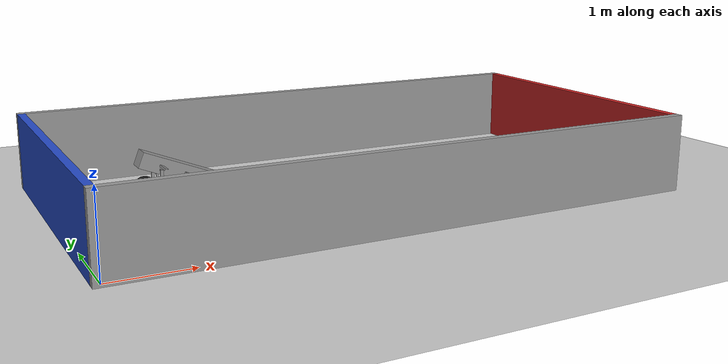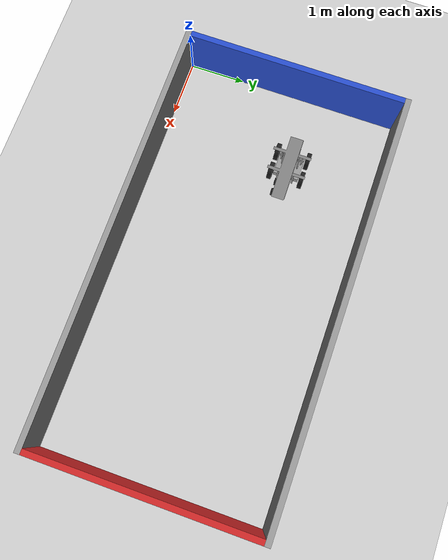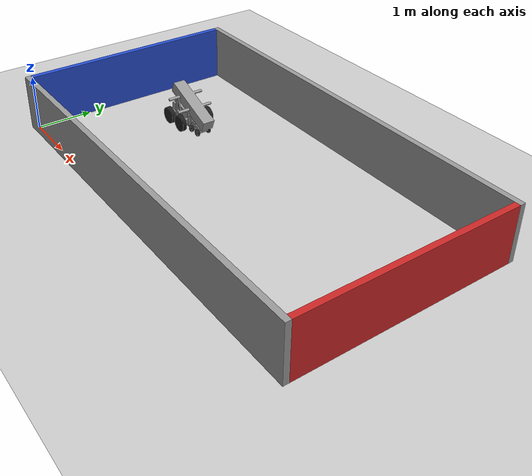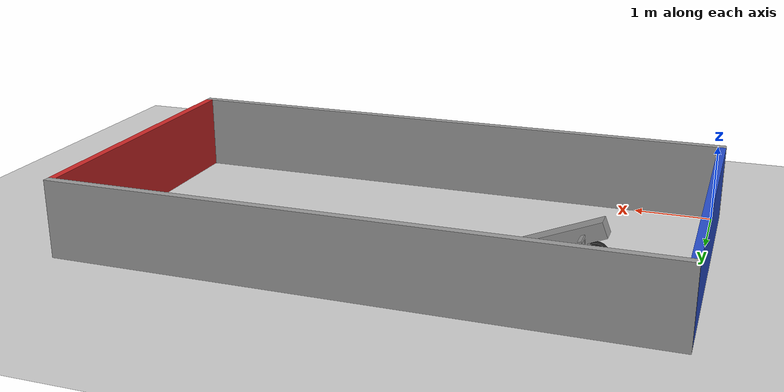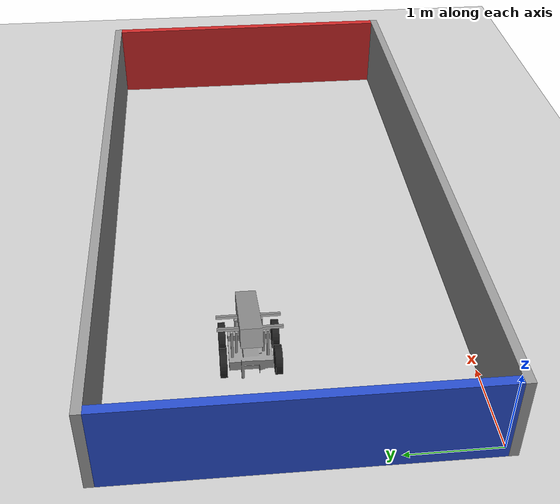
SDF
<sdf version="1.6">
 <world name="default">
  <light name="sun" type="directional">
   <pose>0 0 10 0 -0 0</pose>
   <diffuse>0.8 0.8 0.8 1</diffuse>
   <specular>0.1 0.1 0.1 1</specular>
   <attenuation>
    <range>1000</range>
    <constant>0.9</constant>
    <linear>0.01</linear>
    <quadratic>0.001</quadratic>
   </attenuation>
   <direction>-0.5 0.5 -1</direction>
  </light>
  <model name="ground_plane">
   <static>1</static>
   <link name="link">
    <collision name="collision">
     <geometry><plane><normal>0 0 1</normal><size>100 100</size></plane></geometry>
     <surface><friction><ode><mu>100</mu><mu2>50</mu2></ode></friction></surface>
    </collision>
    <visual name="visual">
     <cast_shadows>0</cast_shadows>
     <geometry><plane><normal>0 0 1</normal><size>100 100</size></plane></geometry>
     <material>
      <script><uri>file://media/materials/scripts/gazebo.material</uri><name>Gazebo/Grey</name></script>
     </material>
    </visual>
   </link>
  </model>
  <gravity>0 0 -9.8</gravity>
  <magnetic_field>6e-06 2.3e-05 -4.2e-05</magnetic_field>
  <atmosphere type="adiabatic"/>
  <physics name="default_physics" default="0" type="ode">
   <max_step_size>0.001</max_step_size>
   <real_time_factor>1</real_time_factor>
   <real_time_update_rate>1000</real_time_update_rate>
  </physics>
  <scene><ambient>0.4 0.4 0.4 1</ambient><background>0.7 0.7 0.7 1</background><shadows>1</shadows></scene>
  <spherical_coordinates>
   <surface_model>EARTH_WGS84</surface_model>
   <latitude_deg>0</latitude_deg>
   <longitude_deg>0</longitude_deg>
   <elevation>0</elevation>
   <heading_deg>0</heading_deg>
  </spherical_coordinates>
  <model name="RMC_Walls_1">
   <link name="mining_wall">
    <pose>3.74 0 0 0 -0 0</pose>
    <inertial>
     <mass>1</mass>
     <inertia>
      <ixx>0.166667</ixx>
      <ixy>0</ixy>
      <ixz>0</ixz>
      <iyy>0.166667</iyy>
      <iyz>0</iyz>
      <izz>0.166667</izz>
     </inertia>
    </inertial>
    <visual name="visual">
     <geometry><box><size>0.1 3.88 1</size></box></geometry>
     <material>
      <lighting>1</lighting>
      <script><uri>file://media/materials/scripts/gazebo.material</uri><name>Gazebo/Red</name></script>
      <ambient>1 0 0 1</ambient>
      <diffuse>0.7 0.7 0.7 1</diffuse>
      <specular>0.01 0.01 0.01 1</specular>
      <emissive>0 0 0 1</emissive>
      <shader type="vertex"><normal_map>__default__</normal_map></shader>
     </material>
    </visual>
    <collision name="collision">
     <geometry><box><size>0.1 3.88 1</size></box></geometry>
     <surface>
      <friction>
       <ode><mu>1</mu><mu2>1</mu2><fdir1>0 0 0</fdir1><slip1>0</slip1><slip2>0</slip2></ode>
       <torsional>
        <coefficient>1</coefficient>
        <patch_radius>0</patch_radius>
        <surface_radius>0</surface_radius>
        <use_patch_radius>1</use_patch_radius>
        <ode><slip>0</slip></ode>
       </torsional>
      </friction>
      <bounce><restitution_coefficient>0</restitution_coefficient><threshold>1e+06</threshold></bounce>
      <contact>
       <collide_without_contact>0</collide_without_contact>
       <collide_without_contact_bitmask>1</collide_without_contact_bitmask>
       <collide_bitmask>1</collide_bitmask>
       <ode>
        <soft_cfm>0</soft_cfm>
        <soft_erp>0.2</soft_erp>
        <kp>1e+13</kp>
        <kd>1</kd>
        <max_vel>0.01</max_vel>
        <min_depth>0</min_depth>
       </ode>
       <bullet>
        <split_impulse>1</split_impulse>
        <split_impulse_penetration_threshold>-0.01</split_impulse_penetration_threshold>
        <soft_cfm>0</soft_cfm>
        <soft_erp>0.2</soft_erp>
        <kp>1e+13</kp>
        <kd>1</kd>
       </bullet>
      </contact>
     </surface>
    </collision>
   </link>
   <link name="collector_wall">
    <pose>-3.74 0 0 0 -0 0</pose>
    <inertial>
     <mass>1</mass>
     <inertia>
      <ixx>0.166667</ixx>
      <ixy>0</ixy>
      <ixz>0</ixz>
      <iyy>0.166667</iyy>
      <iyz>0</iyz>
      <izz>0.166667</izz>
     </inertia>
    </inertial>
    <visual name="visual">
     <geometry><box><size>0.1 3.88 1</size></box></geometry>
     <material>
      <lighting>1</lighting>
      <script><uri>file://media/materials/scripts/gazebo.material</uri><name>Gazebo/Blue</name></script>
      <ambient>0 0 1 1</ambient>
      <diffuse>0.7 0.7 0.7 1</diffuse>
      <specular>0.01 0.01 0.01 1</specular>
      <emissive>0 0 0 1</emissive>
      <shader type="vertex"><normal_map>__default__</normal_map></shader>
     </material>
    </visual>
    <collision name="collision">
     <geometry><box><size>0.1 3.88 1</size></box></geometry>
     <surface>
      <friction>
       <ode><mu>1</mu><mu2>1</mu2><fdir1>0 0 0</fdir1><slip1>0</slip1><slip2>0</slip2></ode>
       <torsional>
        <coefficient>1</coefficient>
        <patch_radius>0</patch_radius>
        <surface_radius>0</surface_radius>
        <use_patch_radius>1</use_patch_radius>
        <ode><slip>0</slip></ode>
       </torsional>
      </friction>
      <bounce><restitution_coefficient>0</restitution_coefficient><threshold>1e+06</threshold></bounce>
      <contact>
       <collide_without_contact>0</collide_without_contact>
       <collide_without_contact_bitmask>1</collide_without_contact_bitmask>
       <collide_bitmask>1</collide_bitmask>
       <ode>
        <soft_cfm>0</soft_cfm>
        <soft_erp>0.2</soft_erp>
        <kp>1e+13</kp>
        <kd>1</kd>
        <max_vel>0.01</max_vel>
        <min_depth>0</min_depth>
       </ode>
       <bullet>
        <split_impulse>1</split_impulse>
        <split_impulse_penetration_threshold>-0.01</split_impulse_penetration_threshold>
        <soft_cfm>0</soft_cfm>
        <soft_erp>0.2</soft_erp>
        <kp>1e+13</kp>
        <kd>1</kd>
       </bullet>
      </contact>
     </surface>
    </collision>
   </link>
   <link name="left_wall">
    <pose>0 1.99 0 0 -0 0</pose>
    <inertial>
     <mass>1</mass>
     <inertia>
      <ixx>0.166667</ixx>
      <ixy>0</ixy>
      <ixz>0</ixz>
      <iyy>0.166667</iyy>
      <iyz>0</iyz>
      <izz>0.166667</izz>
     </inertia>
    </inertial>
    <visual name="visual">
     <geometry><box><size>7.58 0.1 1</size></box></geometry>
     <material>
      <lighting>1</lighting>
      <script><uri>file://media/materials/scripts/gazebo.material</uri><name>Gazebo/Grey</name></script>
      <ambient>0.3 0.3 0.3 1</ambient>
      <diffuse>0.7 0.7 0.7 1</diffuse>
      <specular>0.01 0.01 0.01 1</specular>
      <emissive>0 0 0 1</emissive>
      <shader type="vertex"><normal_map>__default__</normal_map></shader>
     </material>
    </visual>
    <collision name="collision">
     <geometry><box><size>7.58 0.1 1</size></box></geometry>
     <surface>
      <friction>
       <ode><mu>1</mu><mu2>1</mu2><fdir1>0 0 0</fdir1><slip1>0</slip1><slip2>0</slip2></ode>
       <torsional>
        <coefficient>1</coefficient>
        <patch_radius>0</patch_radius>
        <surface_radius>0</surface_radius>
        <use_patch_radius>1</use_patch_radius>
        <ode><slip>0</slip></ode>
       </torsional>
      </friction>
      <bounce><restitution_coefficient>0</restitution_coefficient><threshold>1e+06</threshold></bounce>
      <contact>
       <collide_without_contact>0</collide_without_contact>
       <collide_without_contact_bitmask>1</collide_without_contact_bitmask>
       <collide_bitmask>1</collide_bitmask>
       <ode>
        <soft_cfm>0</soft_cfm>
        <soft_erp>0.2</soft_erp>
        <kp>1e+13</kp>
        <kd>1</kd>
        <max_vel>0.01</max_vel>
        <min_depth>0</min_depth>
       </ode>
       <bullet>
        <split_impulse>1</split_impulse>
        <split_impulse_penetration_threshold>-0.01</split_impulse_penetration_threshold>
        <soft_cfm>0</soft_cfm>
        <soft_erp>0.2</soft_erp>
        <kp>1e+13</kp>
        <kd>1</kd>
       </bullet>
      </contact>
     </surface>
    </collision>
   </link>
   <link name="right_wall">
    <pose>0 -1.99 0 0 -0 0</pose>
    <inertial>
     <mass>1</mass>
     <inertia>
      <ixx>0.166667</ixx>
      <ixy>0</ixy>
      <ixz>0</ixz>
      <iyy>0.166667</iyy>
      <iyz>0</iyz>
      <izz>0.166667</izz>
     </inertia>
    </inertial>
    <visual name="visual">
     <geometry><box><size>7.58 0.1 1</size></box></geometry>
     <material>
      <lighting>1</lighting>
      <script><uri>file://media/materials/scripts/gazebo.material</uri><name>Gazebo/Grey</name></script>
      <ambient>0.3 0.3 0.3 1</ambient>
      <diffuse>0.7 0.7 0.7 1</diffuse>
      <specular>0.01 0.01 0.01 1</specular>
      <emissive>0 0 0 1</emissive>
      <shader type="vertex"><normal_map>__default__</normal_map></shader>
     </material>
    </visual>
    <collision name="collision">
     <geometry><box><size>7.58 0.1 1</size></box></geometry>
     <surface>
      <friction>
       <ode><mu>1</mu><mu2>1</mu2><fdir1>0 0 0</fdir1><slip1>0</slip1><slip2>0</slip2></ode>
       <torsional>
        <coefficient>1</coefficient>
        <patch_radius>0</patch_radius>
        <surface_radius>0</surface_radius>
        <use_patch_radius>1</use_patch_radius>
        <ode><slip>0</slip></ode>
       </torsional>
      </friction>
      <bounce><restitution_coefficient>0</restitution_coefficient><threshold>1e+06</threshold></bounce>
      <contact>
       <collide_without_contact>0</collide_without_contact>
       <collide_without_contact_bitmask>1</collide_without_contact_bitmask>
       <collide_bitmask>1</collide_bitmask>
       <ode>
        <soft_cfm>0</soft_cfm>
        <soft_erp>0.2</soft_erp>
        <kp>1e+13</kp>
        <kd>1</kd>
        <max_vel>0.01</max_vel>
        <min_depth>0</min_depth>
       </ode>
       <bullet>
        <split_impulse>1</split_impulse>
        <split_impulse_penetration_threshold>-0.01</split_impulse_penetration_threshold>
        <soft_cfm>0</soft_cfm>
        <soft_erp>0.2</soft_erp>
        <kp>1e+13</kp>
        <kd>1</kd>
       </bullet>
      </contact>
     </surface>
    </collision>
   </link>
   <static>1</static>
   <pose>3.69 1.94 0.5 0 -0 0</pose>
  </model>
  <model name="transporter_0">
   <link name="base_link">
    <pose>0 0.003 0.1576 0 -0 0</pose>
    <inertial>
     <mass>1</mass>
     <inertia>
      <ixx>0.166667</ixx>
      <ixy>0</ixy>
      <ixz>0</ixz>
      <iyy>0.166667</iyy>
      <iyz>0</iyz>
      <izz>0.166667</izz>
     </inertia>
    </inertial>
    <visual name="visual">
     <geometry>
      <mesh>
       <uri>/home/ssr/ros_kinetic/rmc_dev_ws/src/2018_robot/simulations/gazebo_rmc_sim/models/transporter/minibot_base_link.stl</uri>
       <scale>1 1 1</scale>
      </mesh>
     </geometry>
     <material>
      <lighting>1</lighting>
      <script><uri>file://media/materials/scripts/gazebo.material</uri><name>Gazebo/Grey</name></script>
      <ambient>0.3 0.3 0.3 1</ambient>
      <diffuse>0.7 0.7 0.7 1</diffuse>
      <specular>0.01 0.01 0.01 1</specular>
      <emissive>0 0 0 1</emissive>
      <shader type="vertex"><normal_map>__default__</normal_map></shader>
     </material>
    </visual>
    <collision name="collision_0">
     <geometry>
      <mesh>
       <uri>/home/ssr/ros_kinetic/rmc_dev_ws/src/2018_robot/simulations/gazebo_rmc_sim/models/transporter/minibot_frame_collision.stl</uri>
       <scale>1 1 1</scale>
      </mesh>
     </geometry>
     <surface>
      <friction>
       <ode><mu>1</mu><mu2>1</mu2><fdir1>0 0 0</fdir1><slip1>0</slip1><slip2>0</slip2></ode>
       <torsional>
        <coefficient>1</coefficient>
        <patch_radius>0</patch_radius>
        <surface_radius>0</surface_radius>
        <use_patch_radius>1</use_patch_radius>
        <ode><slip>0</slip></ode>
       </torsional>
      </friction>
      <bounce><restitution_coefficient>0</restitution_coefficient><threshold>1e+06</threshold></bounce>
      <contact>
       <collide_without_contact>0</collide_without_contact>
       <collide_without_contact_bitmask>1</collide_without_contact_bitmask>
       <collide_bitmask>1</collide_bitmask>
       <ode>
        <soft_cfm>0</soft_cfm>
        <soft_erp>0.2</soft_erp>
        <kp>1e+13</kp>
        <kd>1</kd>
        <max_vel>0.01</max_vel>
        <min_depth>0</min_depth>
       </ode>
       <bullet>
        <split_impulse>1</split_impulse>
        <split_impulse_penetration_threshold>-0.01</split_impulse_penetration_threshold>
        <soft_cfm>0</soft_cfm>
        <soft_erp>0.2</soft_erp>
        <kp>1e+13</kp>
        <kd>1</kd>
       </bullet>
      </contact>
     </surface>
    </collision>
   </link>
   <link name="back_left_wheel">
    <pose>-0.1 0.1205 0.085 0 0 -1.5708</pose>
    <inertial>
     <mass>1</mass>
     <inertia>
      <ixx>0.166667</ixx>
      <ixy>0</ixy>
      <ixz>0</ixz>
      <iyy>0.166667</iyy>
      <iyz>0</iyz>
      <izz>0.166667</izz>
     </inertia>
    </inertial>
    <visual name="visual">
     <geometry>
      <mesh>
       <uri>/home/ssr/ros_kinetic/rmc_dev_ws/src/2018_robot/simulations/gazebo_rmc_sim/models/transporter/minibot_wheel.stl</uri>
       <scale>1 1 1</scale>
      </mesh>
     </geometry>
     <material>
      <lighting>1</lighting>
      <script><uri>file://media/materials/scripts/gazebo.material</uri><name>Gazebo/Black</name></script>
      <ambient>0.3 0.3 0.3 1</ambient>
      <diffuse>0.7 0.7 0.7 1</diffuse>
      <specular>0.01 0.01 0.01 1</specular>
      <emissive>0 0 0 1</emissive>
      <shader type="vertex"><normal_map>__default__</normal_map></shader>
     </material>
    </visual>
    <collision name="collision_0">
     <pose>0.0085 0 0 3.14159 1.57079 3.14159</pose>
     <geometry><cylinder><radius>0.06</radius><length>0.037</length></cylinder></geometry>
     <surface>
      <friction>
       <ode><mu>1</mu><mu2>1</mu2><fdir1>0 0 0</fdir1><slip1>0</slip1><slip2>0</slip2></ode>
       <torsional>
        <coefficient>1</coefficient>
        <patch_radius>0</patch_radius>
        <surface_radius>0</surface_radius>
        <use_patch_radius>1</use_patch_radius>
        <ode><slip>0</slip></ode>
       </torsional>
      </friction>
      <bounce><restitution_coefficient>0</restitution_coefficient><threshold>1e+06</threshold></bounce>
      <contact>
       <collide_without_contact>0</collide_without_contact>
       <collide_without_contact_bitmask>1</collide_without_contact_bitmask>
       <collide_bitmask>1</collide_bitmask>
       <ode>
        <soft_cfm>0</soft_cfm>
        <soft_erp>0.2</soft_erp>
        <kp>1e+13</kp>
        <kd>1</kd>
        <max_vel>0.01</max_vel>
        <min_depth>0</min_depth>
       </ode>
       <bullet>
        <split_impulse>1</split_impulse>
        <split_impulse_penetration_threshold>-0.01</split_impulse_penetration_threshold>
        <soft_cfm>0</soft_cfm>
        <soft_erp>0.2</soft_erp>
        <kp>1e+13</kp>
        <kd>1</kd>
       </bullet>
      </contact>
     </surface>
    </collision>
   </link>
   <link name="front_left_wheel">
    <pose>0.1 0.1205 0.085 0 0 -1.5708</pose>
    <inertial>
     <mass>1</mass>
     <inertia>
      <ixx>0.166667</ixx>
      <ixy>0</ixy>
      <ixz>0</ixz>
      <iyy>0.166667</iyy>
      <iyz>0</iyz>
      <izz>0.166667</izz>
     </inertia>
    </inertial>
    <visual name="visual">
     <geometry>
      <mesh>
       <uri>/home/ssr/ros_kinetic/rmc_dev_ws/src/2018_robot/simulations/gazebo_rmc_sim/models/transporter/minibot_wheel.stl</uri>
       <scale>1 1 1</scale>
      </mesh>
     </geometry>
     <material>
      <lighting>1</lighting>
      <script><uri>file://media/materials/scripts/gazebo.material</uri><name>Gazebo/Black</name></script>
      <ambient>0.3 0.3 0.3 1</ambient>
      <diffuse>0.7 0.7 0.7 1</diffuse>
      <specular>0.01 0.01 0.01 1</specular>
      <emissive>0 0 0 1</emissive>
      <shader type="vertex"><normal_map>__default__</normal_map></shader>
     </material>
    </visual>
    <collision name="collision_0">
     <pose>0.0085 0 0 3.14159 1.57079 3.14159</pose>
     <geometry><cylinder><radius>0.06</radius><length>0.037</length></cylinder></geometry>
     <surface>
      <friction>
       <ode><mu>1</mu><mu2>1</mu2><fdir1>0 0 0</fdir1><slip1>0</slip1><slip2>0</slip2></ode>
       <torsional>
        <coefficient>1</coefficient>
        <patch_radius>0</patch_radius>
        <surface_radius>0</surface_radius>
        <use_patch_radius>1</use_patch_radius>
        <ode><slip>0</slip></ode>
       </torsional>
      </friction>
      <bounce><restitution_coefficient>0</restitution_coefficient><threshold>1e+06</threshold></bounce>
      <contact>
       <collide_without_contact>0</collide_without_contact>
       <collide_without_contact_bitmask>1</collide_without_contact_bitmask>
       <collide_bitmask>1</collide_bitmask>
       <ode>
        <soft_cfm>0</soft_cfm>
        <soft_erp>0.2</soft_erp>
        <kp>1e+13</kp>
        <kd>1</kd>
        <max_vel>0.01</max_vel>
        <min_depth>0</min_depth>
       </ode>
       <bullet>
        <split_impulse>1</split_impulse>
        <split_impulse_penetration_threshold>-0.01</split_impulse_penetration_threshold>
        <soft_cfm>0</soft_cfm>
        <soft_erp>0.2</soft_erp>
        <kp>1e+13</kp>
        <kd>1</kd>
       </bullet>
      </contact>
     </surface>
    </collision>
   </link>
   <link name="front_right_wheel">
    <pose>0.1 -0.122 0.085 0 -0 1.5708</pose>
    <inertial>
     <mass>1</mass>
     <inertia>
      <ixx>0.166667</ixx>
      <ixy>0</ixy>
      <ixz>0</ixz>
      <iyy>0.166667</iyy>
      <iyz>0</iyz>
      <izz>0.166667</izz>
     </inertia>
    </inertial>
    <visual name="visual">
     <geometry>
      <mesh>
       <uri>/home/ssr/ros_kinetic/rmc_dev_ws/src/2018_robot/simulations/gazebo_rmc_sim/models/transporter/minibot_wheel.stl</uri>
       <scale>1 1 1</scale>
      </mesh>
     </geometry>
     <material>
      <lighting>1</lighting>
      <script><uri>file://media/materials/scripts/gazebo.material</uri><name>Gazebo/Black</name></script>
      <ambient>0.3 0.3 0.3 1</ambient>
      <diffuse>0.7 0.7 0.7 1</diffuse>
      <specular>0.01 0.01 0.01 1</specular>
      <emissive>0 0 0 1</emissive>
      <shader type="vertex"><normal_map>__default__</normal_map></shader>
     </material>
    </visual>
    <collision name="collision_0">
     <pose>0.0085 0 0 3.14159 1.57079 3.14159</pose>
     <geometry><cylinder><radius>0.06</radius><length>0.037</length></cylinder></geometry>
     <surface>
      <friction>
       <ode><mu>1</mu><mu2>1</mu2><fdir1>0 0 0</fdir1><slip1>0</slip1><slip2>0</slip2></ode>
       <torsional>
        <coefficient>1</coefficient>
        <patch_radius>0</patch_radius>
        <surface_radius>0</surface_radius>
        <use_patch_radius>1</use_patch_radius>
        <ode><slip>0</slip></ode>
       </torsional>
      </friction>
      <bounce><restitution_coefficient>0</restitution_coefficient><threshold>1e+06</threshold></bounce>
      <contact>
       <collide_without_contact>0</collide_without_contact>
       <collide_without_contact_bitmask>1</collide_without_contact_bitmask>
       <collide_bitmask>1</collide_bitmask>
       <ode>
        <soft_cfm>0</soft_cfm>
        <soft_erp>0.2</soft_erp>
        <kp>1e+13</kp>
        <kd>1</kd>
        <max_vel>0.01</max_vel>
        <min_depth>0</min_depth>
       </ode>
       <bullet>
        <split_impulse>1</split_impulse>
        <split_impulse_penetration_threshold>-0.01</split_impulse_penetration_threshold>
        <soft_cfm>0</soft_cfm>
        <soft_erp>0.2</soft_erp>
        <kp>1e+13</kp>
        <kd>1</kd>
       </bullet>
      </contact>
     </surface>
    </collision>
   </link>
   <link name="back_right_wheel">
    <pose>-0.1 -0.122 0.085 0 -0 1.5708</pose>
    <inertial>
     <mass>1</mass>
     <inertia>
      <ixx>0.166667</ixx>
      <ixy>0</ixy>
      <ixz>0</ixz>
      <iyy>0.166667</iyy>
      <iyz>0</iyz>
      <izz>0.166667</izz>
     </inertia>
    </inertial>
    <visual name="visual">
     <geometry>
      <mesh>
       <uri>/home/ssr/ros_kinetic/rmc_dev_ws/src/2018_robot/simulations/gazebo_rmc_sim/models/transporter/minibot_wheel.stl</uri>
       <scale>1 1 1</scale>
      </mesh>
     </geometry>
     <material>
      <lighting>1</lighting>
      <script><uri>file://media/materials/scripts/gazebo.material</uri><name>Gazebo/Black</name></script>
      <ambient>0.3 0.3 0.3 1</ambient>
      <diffuse>0.7 0.7 0.7 1</diffuse>
      <specular>0.01 0.01 0.01 1</specular>
      <emissive>0 0 0 1</emissive>
      <shader type="vertex"><normal_map>__default__</normal_map></shader>
     </material>
    </visual>
    <collision name="collision_0">
     <pose>0.0085 0 0 3.14159 1.57079 3.14159</pose>
     <geometry><cylinder><radius>0.06</radius><length>0.037</length></cylinder></geometry>
     <surface>
      <friction>
       <ode><mu>1</mu><mu2>1</mu2><fdir1>0 0 0</fdir1><slip1>0</slip1><slip2>0</slip2></ode>
       <torsional>
        <coefficient>1</coefficient>
        <patch_radius>0</patch_radius>
        <surface_radius>0</surface_radius>
        <use_patch_radius>1</use_patch_radius>
        <ode><slip>0</slip></ode>
       </torsional>
      </friction>
      <bounce><restitution_coefficient>0</restitution_coefficient><threshold>1e+06</threshold></bounce>
      <contact>
       <collide_without_contact>0</collide_without_contact>
       <collide_without_contact_bitmask>1</collide_without_contact_bitmask>
       <collide_bitmask>1</collide_bitmask>
       <ode>
        <soft_cfm>0</soft_cfm>
        <soft_erp>0.2</soft_erp>
        <kp>1e+13</kp>
        <kd>1</kd>
        <max_vel>0.01</max_vel>
        <min_depth>0</min_depth>
       </ode>
       <bullet>
        <split_impulse>1</split_impulse>
        <split_impulse_penetration_threshold>-0.01</split_impulse_penetration_threshold>
        <soft_cfm>0</soft_cfm>
        <soft_erp>0.2</soft_erp>
        <kp>1e+13</kp>
        <kd>1</kd>
       </bullet>
      </contact>
     </surface>
    </collision>
   </link>
   <joint name="BL_Wheel" type="revolute">
    <parent>base_link</parent>
    <child>back_left_wheel</child>
    <axis>
     <xyz>1 0 0</xyz>
     <use_parent_model_frame>0</use_parent_model_frame>
     <limit>
      <lower>-1.79769e+308</lower>
      <upper>1.79769e+308</upper>
      <effort>-1</effort>
      <velocity>1</velocity>
     </limit>
     <dynamics>
      <spring_reference>0</spring_reference>
      <spring_stiffness>0</spring_stiffness>
      <damping>10</damping>
      <friction>1</friction>
     </dynamics>
    </axis>
    <physics>
     <ode><limit><cfm>0</cfm><erp>0.2</erp></limit><suspension><cfm>0</cfm><erp>0.2</erp></suspension></ode>
    </physics>
   </joint>
   <joint name="FL_Wheel" type="revolute">
    <parent>base_link</parent>
    <child>front_left_wheel</child>
    <axis>
     <xyz>1 0 0</xyz>
     <use_parent_model_frame>0</use_parent_model_frame>
     <limit>
      <lower>-1.79769e+308</lower>
      <upper>1.79769e+308</upper>
      <effort>-1</effort>
      <velocity>1</velocity>
     </limit>
     <dynamics>
      <spring_reference>0</spring_reference>
      <spring_stiffness>0</spring_stiffness>
      <damping>10</damping>
      <friction>1</friction>
     </dynamics>
    </axis>
    <physics>
     <ode><limit><cfm>0</cfm><erp>0.2</erp></limit><suspension><cfm>0</cfm><erp>0.2</erp></suspension></ode>
    </physics>
   </joint>
   <joint name="BR_Wheel" type="revolute">
    <parent>base_link</parent>
    <child>back_right_wheel</child>
    <axis>
     <xyz>1 0 0</xyz>
     <use_parent_model_frame>0</use_parent_model_frame>
     <limit>
      <lower>-1.79769e+308</lower>
      <upper>1.79769e+308</upper>
      <effort>-1</effort>
      <velocity>1</velocity>
     </limit>
     <dynamics>
      <spring_reference>0</spring_reference>
      <spring_stiffness>0</spring_stiffness>
      <damping>10</damping>
      <friction>1</friction>
     </dynamics>
    </axis>
    <physics>
     <ode><limit><cfm>0</cfm><erp>0.2</erp></limit><suspension><cfm>0</cfm><erp>0.2</erp></suspension></ode>
    </physics>
   </joint>
   <joint name="FR_Wheel" type="revolute">
    <parent>base_link</parent>
    <child>front_right_wheel</child>
    <axis>
     <xyz>1 0 0</xyz>
     <use_parent_model_frame>0</use_parent_model_frame>
     <limit>
      <lower>-1.79769e+308</lower>
      <upper>1.79769e+308</upper>
      <effort>-1</effort>
      <velocity>1</velocity>
     </limit>
     <dynamics>
      <spring_reference>0</spring_reference>
      <spring_stiffness>0</spring_stiffness>
      <damping>10</damping>
      <friction>1</friction>
     </dynamics>
    </axis>
    <physics>
     <ode><limit><cfm>0</cfm><erp>0.2</erp></limit><suspension><cfm>0</cfm><erp>0.2</erp></suspension></ode>
    </physics>
   </joint>
   <static>0</static>
   <pose>1.8074 2.319 -0.025008 -8e-06 -1e-06 -0.001156</pose>
  </model>
  <model name="Digger_3">
   <link name="base_link">
    <pose>-0.180752 0.18451 -0.096283 0 -0 0</pose>
    <inertial>
     <mass>30</mass>
     <inertia>
      <ixx>0.166667</ixx>
      <ixy>0</ixy>
      <ixz>0</ixz>
      <iyy>0.166667</iyy>
      <iyz>0</iyz>
      <izz>0.166667</izz>
     </inertia>
    </inertial>
    <visual name="visual">
     <pose>0 0 0 1.5708 0 -1.5708</pose>
     <geometry>
      <mesh>
       <uri>/home/ssr/ros_kinetic/rmc_dev_ws/src/2018_robot/simulations/gazebo_rmc_sim/models/Digger/Simple_Chassis.stl</uri>
       <scale>0.001 0.001 0.001</scale>
      </mesh>
     </geometry>
     <material>
      <lighting>1</lighting>
      <script><uri>file://media/materials/scripts/gazebo.material</uri><name>Gazebo/Grey</name></script>
      <ambient>0.3 0.3 0.3 1</ambient>
      <diffuse>0.7 0.7 0.7 1</diffuse>
      <specular>0.01 0.01 0.01 1</specular>
      <emissive>0 0 0 1</emissive>
      <shader type="vertex"><normal_map>__default__</normal_map></shader>
     </material>
    </visual>
    <collision name="collision">
     <pose>0 0 0 1.5708 0 -1.5708</pose>
     <geometry>
      <mesh>
       <uri>/home/ssr/ros_kinetic/rmc_dev_ws/src/2018_robot/simulations/gazebo_rmc_sim/models/Digger/Simple_Chassis.stl</uri>
       <scale>0.001 0.001 0.001</scale>
      </mesh>
     </geometry>
     <surface>
      <friction>
       <ode><mu>1</mu><mu2>1</mu2><fdir1>0 0 0</fdir1><slip1>0</slip1><slip2>0</slip2></ode>
       <torsional>
        <coefficient>1</coefficient>
        <patch_radius>0</patch_radius>
        <surface_radius>0</surface_radius>
        <use_patch_radius>1</use_patch_radius>
        <ode><slip>0</slip></ode>
       </torsional>
      </friction>
      <bounce><restitution_coefficient>0</restitution_coefficient><threshold>1e+06</threshold></bounce>
      <contact>
       <collide_without_contact>0</collide_without_contact>
       <collide_without_contact_bitmask>1</collide_without_contact_bitmask>
       <collide_bitmask>1</collide_bitmask>
       <ode>
        <soft_cfm>0</soft_cfm>
        <soft_erp>0.2</soft_erp>
        <kp>1e+13</kp>
        <kd>1</kd>
        <max_vel>0.01</max_vel>
        <min_depth>0</min_depth>
       </ode>
       <bullet>
        <split_impulse>1</split_impulse>
        <split_impulse_penetration_threshold>-0.01</split_impulse_penetration_threshold>
        <soft_cfm>0</soft_cfm>
        <soft_erp>0.2</soft_erp>
        <kp>1e+13</kp>
        <kd>1</kd>
       </bullet>
      </contact>
     </surface>
    </collision>
   </link>
   <link name="arm">
    <pose>-0.325179 0.069854 0.358325 1.19198 -0 -1.5708</pose>
    <inertial>
     <mass>1</mass>
     <inertia>
      <ixx>0.166667</ixx>
      <ixy>0</ixy>
      <ixz>0</ixz>
      <iyy>0.166667</iyy>
      <iyz>0</iyz>
      <izz>0.166667</izz>
     </inertia>
    </inertial>
    <visual name="visual">
     <geometry>
      <mesh>
       <uri>/home/ssr/ros_kinetic/rmc_dev_ws/src/2018_robot/simulations/gazebo_rmc_sim/models/Digger/Simple_Arm.stl</uri>
       <scale>0.001 0.001 0.001</scale>
      </mesh>
     </geometry>
     <material>
      <lighting>1</lighting>
      <script><uri>file://media/materials/scripts/gazebo.material</uri><name>Gazebo/Grey</name></script>
      <ambient>0.3 0.3 0.3 1</ambient>
      <diffuse>0.7 0.7 0.7 1</diffuse>
      <specular>0.01 0.01 0.01 1</specular>
      <emissive>0 0 0 1</emissive>
      <shader type="vertex"><normal_map>__default__</normal_map></shader>
     </material>
    </visual>
   </link>
   <link name="back_left_actuator_bottom">
    <pose>-0.080752 0.146804 -0.01705 0 0.072198 0</pose>
    <inertial>
     <mass>1</mass>
     <inertia>
      <ixx>0.166667</ixx>
      <ixy>0</ixy>
      <ixz>0</ixz>
      <iyy>0.166667</iyy>
      <iyz>0</iyz>
      <izz>0.166667</izz>
     </inertia>
    </inertial>
    <visual name="visual">
     <pose>0 0 0.17195 0 -0 0</pose>
     <geometry><box><size>0.0381 0.0254 0.3429</size></box></geometry>
     <material>
      <lighting>1</lighting>
      <script><uri>file://media/materials/scripts/gazebo.material</uri><name>Gazebo/Grey</name></script>
      <ambient>0.3 0.3 0.3 1</ambient>
      <diffuse>0.7 0.7 0.7 1</diffuse>
      <specular>0.01 0.01 0.01 1</specular>
      <emissive>0 0 0 1</emissive>
      <shader type="vertex"><normal_map>__default__</normal_map></shader>
     </material>
    </visual>
    <collision name="collision">
     <pose>0 0 0.17195 0 -0 0</pose>
     <geometry><box><size>0.0381 0.0254 0.3429</size></box></geometry>
     <surface>
      <friction>
       <ode><mu>1</mu><mu2>1</mu2><fdir1>0 0 0</fdir1><slip1>0</slip1><slip2>0</slip2></ode>
       <torsional>
        <coefficient>1</coefficient>
        <patch_radius>0</patch_radius>
        <surface_radius>0</surface_radius>
        <use_patch_radius>1</use_patch_radius>
        <ode><slip>0</slip></ode>
       </torsional>
      </friction>
      <bounce><restitution_coefficient>0</restitution_coefficient><threshold>1e+06</threshold></bounce>
      <contact>
       <collide_without_contact>0</collide_without_contact>
       <collide_without_contact_bitmask>1</collide_without_contact_bitmask>
       <collide_bitmask>1</collide_bitmask>
       <ode>
        <soft_cfm>0</soft_cfm>
        <soft_erp>0.2</soft_erp>
        <kp>1e+13</kp>
        <kd>1</kd>
        <max_vel>0.01</max_vel>
        <min_depth>0</min_depth>
       </ode>
       <bullet>
        <split_impulse>1</split_impulse>
        <split_impulse_penetration_threshold>-0.01</split_impulse_penetration_threshold>
        <soft_cfm>0</soft_cfm>
        <soft_erp>0.2</soft_erp>
        <kp>1e+13</kp>
        <kd>1</kd>
       </bullet>
      </contact>
     </surface>
    </collision>
   </link>
   <link name="back_left_actuator_top">
    <pose>-0.080752 0.146804 -0.01705 0 0.072198 0</pose>
    <inertial>
     <mass>1</mass>
     <inertia>
      <ixx>0.166667</ixx>
      <ixy>0</ixy>
      <ixz>0</ixz>
      <iyy>0.166667</iyy>
      <iyz>0</iyz>
      <izz>0.166667</izz>
     </inertia>
    </inertial>
    <visual name="visual">
     <pose>0 0 0.17195 0 -0 0</pose>
     <geometry><box><size>0.0381 0.0254 0.3429</size></box></geometry>
     <material>
      <lighting>1</lighting>
      <script><uri>file://media/materials/scripts/gazebo.material</uri><name>Gazebo/Red</name></script>
      <ambient>0.3 0.3 0.3 1</ambient>
      <diffuse>0.7 0.7 0.7 1</diffuse>
      <specular>0.01 0.01 0.01 1</specular>
      <emissive>0 0 0 1</emissive>
      <shader type="vertex"><normal_map>__default__</normal_map></shader>
     </material>
    </visual>
    <collision name="collision">
     <pose>0 0 0.17195 0 -0 0</pose>
     <geometry><box><size>0.0381 0.0254 0.3429</size></box></geometry>
     <surface>
      <friction>
       <ode><mu>1</mu><mu2>1</mu2><fdir1>0 0 0</fdir1><slip1>0</slip1><slip2>0</slip2></ode>
       <torsional>
        <coefficient>1</coefficient>
        <patch_radius>0</patch_radius>
        <surface_radius>0</surface_radius>
        <use_patch_radius>1</use_patch_radius>
        <ode><slip>0</slip></ode>
       </torsional>
      </friction>
      <bounce><restitution_coefficient>0</restitution_coefficient><threshold>1e+06</threshold></bounce>
      <contact>
       <collide_without_contact>0</collide_without_contact>
       <collide_without_contact_bitmask>1</collide_without_contact_bitmask>
       <collide_bitmask>1</collide_bitmask>
       <ode>
        <soft_cfm>0</soft_cfm>
        <soft_erp>0.2</soft_erp>
        <kp>1e+13</kp>
        <kd>1</kd>
        <max_vel>0.01</max_vel>
        <min_depth>0</min_depth>
       </ode>
       <bullet>
        <split_impulse>1</split_impulse>
        <split_impulse_penetration_threshold>-0.01</split_impulse_penetration_threshold>
        <soft_cfm>0</soft_cfm>
        <soft_erp>0.2</soft_erp>
        <kp>1e+13</kp>
        <kd>1</kd>
       </bullet>
      </contact>
     </surface>
    </collision>
   </link>
   <link name="back_right_actuator_bottom">
    <pose>-0.080752 -0.225027 -0.01705 0 0.072198 0</pose>
    <inertial>
     <mass>1</mass>
     <inertia>
      <ixx>0.166667</ixx>
      <ixy>0</ixy>
      <ixz>0</ixz>
      <iyy>0.166667</iyy>
      <iyz>0</iyz>
      <izz>0.166667</izz>
     </inertia>
    </inertial>
    <visual name="visual">
     <pose>0 0 0.17195 0 -0 0</pose>
     <geometry><box><size>0.0381 0.0254 0.3429</size></box></geometry>
     <material>
      <lighting>1</lighting>
      <script><uri>file://media/materials/scripts/gazebo.material</uri><name>Gazebo/Grey</name></script>
      <ambient>0.3 0.3 0.3 1</ambient>
      <diffuse>0.7 0.7 0.7 1</diffuse>
      <specular>0.01 0.01 0.01 1</specular>
      <emissive>0 0 0 1</emissive>
      <shader type="vertex"><normal_map>__default__</normal_map></shader>
     </material>
    </visual>
    <collision name="collision">
     <pose>0 0 0.17195 0 -0 0</pose>
     <geometry><box><size>0.0381 0.0254 0.3429</size></box></geometry>
     <surface>
      <friction>
       <ode><mu>1</mu><mu2>1</mu2><fdir1>0 0 0</fdir1><slip1>0</slip1><slip2>0</slip2></ode>
       <torsional>
        <coefficient>1</coefficient>
        <patch_radius>0</patch_radius>
        <surface_radius>0</surface_radius>
        <use_patch_radius>1</use_patch_radius>
        <ode><slip>0</slip></ode>
       </torsional>
      </friction>
      <bounce><restitution_coefficient>0</restitution_coefficient><threshold>1e+06</threshold></bounce>
      <contact>
       <collide_without_contact>0</collide_without_contact>
       <collide_without_contact_bitmask>1</collide_without_contact_bitmask>
       <collide_bitmask>1</collide_bitmask>
       <ode>
        <soft_cfm>0</soft_cfm>
        <soft_erp>0.2</soft_erp>
        <kp>1e+13</kp>
        <kd>1</kd>
        <max_vel>0.01</max_vel>
        <min_depth>0</min_depth>
       </ode>
       <bullet>
        <split_impulse>1</split_impulse>
        <split_impulse_penetration_threshold>-0.01</split_impulse_penetration_threshold>
        <soft_cfm>0</soft_cfm>
        <soft_erp>0.2</soft_erp>
        <kp>1e+13</kp>
        <kd>1</kd>
       </bullet>
      </contact>
     </surface>
    </collision>
   </link>
   <link name="back_right_actuator_top">
    <pose>-0.080752 -0.225027 -0.01705 0 0.072198 0</pose>
    <inertial>
     <mass>1</mass>
     <inertia>
      <ixx>0.166667</ixx>
      <ixy>0</ixy>
      <ixz>0</ixz>
      <iyy>0.166667</iyy>
      <iyz>0</iyz>
      <izz>0.166667</izz>
     </inertia>
    </inertial>
    <visual name="visual">
     <pose>0 0 0.17195 0 -0 0</pose>
     <geometry><box><size>0.0381 0.0254 0.3429</size></box></geometry>
     <material>
      <lighting>1</lighting>
      <script><uri>file://media/materials/scripts/gazebo.material</uri><name>Gazebo/Red</name></script>
      <ambient>0.3 0.3 0.3 1</ambient>
      <diffuse>0.7 0.7 0.7 1</diffuse>
      <specular>0.01 0.01 0.01 1</specular>
      <emissive>0 0 0 1</emissive>
      <shader type="vertex"><normal_map>__default__</normal_map></shader>
     </material>
    </visual>
    <collision name="collision">
     <pose>0 0 0.17195 0 -0 0</pose>
     <geometry><box><size>0.0381 0.0254 0.3429</size></box></geometry>
     <surface>
      <friction>
       <ode><mu>1</mu><mu2>1</mu2><fdir1>0 0 0</fdir1><slip1>0</slip1><slip2>0</slip2></ode>
       <torsional>
        <coefficient>1</coefficient>
        <patch_radius>0</patch_radius>
        <surface_radius>0</surface_radius>
        <use_patch_radius>1</use_patch_radius>
        <ode><slip>0</slip></ode>
       </torsional>
      </friction>
      <bounce><restitution_coefficient>0</restitution_coefficient><threshold>1e+06</threshold></bounce>
      <contact>
       <collide_without_contact>0</collide_without_contact>
       <collide_without_contact_bitmask>1</collide_without_contact_bitmask>
       <collide_bitmask>1</collide_bitmask>
       <ode>
        <soft_cfm>0</soft_cfm>
        <soft_erp>0.2</soft_erp>
        <kp>1e+13</kp>
        <kd>1</kd>
        <max_vel>0.01</max_vel>
        <min_depth>0</min_depth>
       </ode>
       <bullet>
        <split_impulse>1</split_impulse>
        <split_impulse_penetration_threshold>-0.01</split_impulse_penetration_threshold>
        <soft_cfm>0</soft_cfm>
        <soft_erp>0.2</soft_erp>
        <kp>1e+13</kp>
        <kd>1</kd>
       </bullet>
      </contact>
     </surface>
    </collision>
   </link>
   <link name="front_left_actuator_bottom">
    <pose>0.299248 0.09451 -0.079616 0 -0.097496 0</pose>
    <inertial>
     <mass>1</mass>
     <inertia>
      <ixx>0.166667</ixx>
      <ixy>0</ixy>
      <ixz>0</ixz>
      <iyy>0.166667</iyy>
      <iyz>0</iyz>
      <izz>0.166667</izz>
     </inertia>
    </inertial>
    <visual name="visual">
     <pose>0 0 0.133333 0 -0 0</pose>
     <geometry><box><size>0.0381 0.0254 0.266667</size></box></geometry>
     <material>
      <lighting>1</lighting>
      <script><uri>file://media/materials/scripts/gazebo.material</uri><name>Gazebo/Grey</name></script>
      <ambient>0.3 0.3 0.3 1</ambient>
      <diffuse>0.7 0.7 0.7 1</diffuse>
      <specular>0.01 0.01 0.01 1</specular>
      <emissive>0 0 0 1</emissive>
      <shader type="vertex"><normal_map>__default__</normal_map></shader>
     </material>
    </visual>
    <collision name="collision">
     <pose>0 0 0.133333 0 -0 0</pose>
     <geometry><box><size>0.0381 0.0254 0.266667</size></box></geometry>
     <surface>
      <friction>
       <ode><mu>1</mu><mu2>1</mu2><fdir1>0 0 0</fdir1><slip1>0</slip1><slip2>0</slip2></ode>
       <torsional>
        <coefficient>1</coefficient>
        <patch_radius>0</patch_radius>
        <surface_radius>0</surface_radius>
        <use_patch_radius>1</use_patch_radius>
        <ode><slip>0</slip></ode>
       </torsional>
      </friction>
      <bounce><restitution_coefficient>0</restitution_coefficient><threshold>1e+06</threshold></bounce>
      <contact>
       <collide_without_contact>0</collide_without_contact>
       <collide_without_contact_bitmask>1</collide_without_contact_bitmask>
       <collide_bitmask>1</collide_bitmask>
       <ode>
        <soft_cfm>0</soft_cfm>
        <soft_erp>0.2</soft_erp>
        <kp>1e+13</kp>
        <kd>1</kd>
        <max_vel>0.01</max_vel>
        <min_depth>0</min_depth>
       </ode>
       <bullet>
        <split_impulse>1</split_impulse>
        <split_impulse_penetration_threshold>-0.01</split_impulse_penetration_threshold>
        <soft_cfm>0</soft_cfm>
        <soft_erp>0.2</soft_erp>
        <kp>1e+13</kp>
        <kd>1</kd>
       </bullet>
      </contact>
     </surface>
    </collision>
   </link>
   <link name="front_left_actuator_top">
    <pose>0.299248 0.09451 -0.079616 0 -0.097496 0</pose>
    <inertial>
     <mass>1</mass>
     <inertia>
      <ixx>0.166667</ixx>
      <ixy>0</ixy>
      <ixz>0</ixz>
      <iyy>0.166667</iyy>
      <iyz>0</iyz>
      <izz>0.166667</izz>
     </inertia>
    </inertial>
    <visual name="visual">
     <pose>0 0 0.133333 0 -0 0</pose>
     <geometry><box><size>0.0381 0.0254 0.266667</size></box></geometry>
     <material>
      <lighting>1</lighting>
      <script><uri>file://media/materials/scripts/gazebo.material</uri><name>Gazebo/Red</name></script>
      <ambient>0.3 0.3 0.3 1</ambient>
      <diffuse>0.7 0.7 0.7 1</diffuse>
      <specular>0.01 0.01 0.01 1</specular>
      <emissive>0 0 0 1</emissive>
      <shader type="vertex"><normal_map>__default__</normal_map></shader>
     </material>
    </visual>
    <collision name="collision">
     <pose>0 0 0.133333 0 -0 0</pose>
     <geometry><box><size>0.0381 0.0254 0.266667</size></box></geometry>
     <surface>
      <friction>
       <ode><mu>1</mu><mu2>1</mu2><fdir1>0 0 0</fdir1><slip1>0</slip1><slip2>0</slip2></ode>
       <torsional>
        <coefficient>1</coefficient>
        <patch_radius>0</patch_radius>
        <surface_radius>0</surface_radius>
        <use_patch_radius>1</use_patch_radius>
        <ode><slip>0</slip></ode>
       </torsional>
      </friction>
      <bounce><restitution_coefficient>0</restitution_coefficient><threshold>1e+06</threshold></bounce>
      <contact>
       <collide_without_contact>0</collide_without_contact>
       <collide_without_contact_bitmask>1</collide_without_contact_bitmask>
       <collide_bitmask>1</collide_bitmask>
       <ode>
        <soft_cfm>0</soft_cfm>
        <soft_erp>0.2</soft_erp>
        <kp>1e+13</kp>
        <kd>1</kd>
        <max_vel>0.01</max_vel>
        <min_depth>0</min_depth>
       </ode>
       <bullet>
        <split_impulse>1</split_impulse>
        <split_impulse_penetration_threshold>-0.01</split_impulse_penetration_threshold>
        <soft_cfm>0</soft_cfm>
        <soft_erp>0.2</soft_erp>
        <kp>1e+13</kp>
        <kd>1</kd>
       </bullet>
      </contact>
     </surface>
    </collision>
   </link>
   <link name="front_right_actuator_bottom">
    <pose>0.299248 -0.18549 -0.079616 0 -0.097496 0</pose>
    <inertial>
     <mass>1</mass>
     <inertia>
      <ixx>0.166667</ixx>
      <ixy>0</ixy>
      <ixz>0</ixz>
      <iyy>0.166667</iyy>
      <iyz>0</iyz>
      <izz>0.166667</izz>
     </inertia>
    </inertial>
    <visual name="visual">
     <pose>0 0 0.133333 0 -0 0</pose>
     <geometry><box><size>0.0381 0.0254 0.266667</size></box></geometry>
     <material>
      <lighting>1</lighting>
      <script><uri>file://media/materials/scripts/gazebo.material</uri><name>Gazebo/Grey</name></script>
      <ambient>0.3 0.3 0.3 1</ambient>
      <diffuse>0.7 0.7 0.7 1</diffuse>
      <specular>0.01 0.01 0.01 1</specular>
      <emissive>0 0 0 1</emissive>
      <shader type="vertex"><normal_map>__default__</normal_map></shader>
     </material>
    </visual>
    <collision name="collision">
     <pose>0 0 0.133333 0 -0 0</pose>
     <geometry><box><size>0.0381 0.0254 0.266667</size></box></geometry>
     <surface>
      <friction>
       <ode><mu>1</mu><mu2>1</mu2><fdir1>0 0 0</fdir1><slip1>0</slip1><slip2>0</slip2></ode>
       <torsional>
        <coefficient>1</coefficient>
        <patch_radius>0</patch_radius>
        <surface_radius>0</surface_radius>
        <use_patch_radius>1</use_patch_radius>
        <ode><slip>0</slip></ode>
       </torsional>
      </friction>
      <bounce><restitution_coefficient>0</restitution_coefficient><threshold>1e+06</threshold></bounce>
      <contact>
       <collide_without_contact>0</collide_without_contact>
       <collide_without_contact_bitmask>1</collide_without_contact_bitmask>
       <collide_bitmask>1</collide_bitmask>
       <ode>
        <soft_cfm>0</soft_cfm>
        <soft_erp>0.2</soft_erp>
        <kp>1e+13</kp>
        <kd>1</kd>
        <max_vel>0.01</max_vel>
        <min_depth>0</min_depth>
       </ode>
       <bullet>
        <split_impulse>1</split_impulse>
        <split_impulse_penetration_threshold>-0.01</split_impulse_penetration_threshold>
        <soft_cfm>0</soft_cfm>
        <soft_erp>0.2</soft_erp>
        <kp>1e+13</kp>
        <kd>1</kd>
       </bullet>
      </contact>
     </surface>
    </collision>
   </link>
   <link name="front_right_actuator_top">
    <pose>0.299248 -0.18549 -0.079616 0 -0.097496 0</pose>
    <inertial>
     <mass>1</mass>
     <inertia>
      <ixx>0.166667</ixx>
      <ixy>0</ixy>
      <ixz>0</ixz>
      <iyy>0.166667</iyy>
      <iyz>0</iyz>
      <izz>0.166667</izz>
     </inertia>
    </inertial>
    <visual name="visual">
     <pose>0 0 0.133333 0 -0 0</pose>
     <geometry><box><size>0.0381 0.0254 0.266667</size></box></geometry>
     <material>
      <lighting>1</lighting>
      <script><uri>file://media/materials/scripts/gazebo.material</uri><name>Gazebo/Red</name></script>
      <ambient>0.3 0.3 0.3 1</ambient>
      <diffuse>0.7 0.7 0.7 1</diffuse>
      <specular>0.01 0.01 0.01 1</specular>
      <emissive>0 0 0 1</emissive>
      <shader type="vertex"><normal_map>__default__</normal_map></shader>
     </material>
    </visual>
    <collision name="collision">
     <pose>0 0 0.133333 0 -0 0</pose>
     <geometry><box><size>0.0381 0.0254 0.266667</size></box></geometry>
     <surface>
      <friction>
       <ode><mu>1</mu><mu2>1</mu2><fdir1>0 0 0</fdir1><slip1>0</slip1><slip2>0</slip2></ode>
       <torsional>
        <coefficient>1</coefficient>
        <patch_radius>0</patch_radius>
        <surface_radius>0</surface_radius>
        <use_patch_radius>1</use_patch_radius>
        <ode><slip>0</slip></ode>
       </torsional>
      </friction>
      <bounce><restitution_coefficient>0</restitution_coefficient><threshold>1e+06</threshold></bounce>
      <contact>
       <collide_without_contact>0</collide_without_contact>
       <collide_without_contact_bitmask>1</collide_without_contact_bitmask>
       <collide_bitmask>1</collide_bitmask>
       <ode>
        <soft_cfm>0</soft_cfm>
        <soft_erp>0.2</soft_erp>
        <kp>1e+13</kp>
        <kd>1</kd>
        <max_vel>0.01</max_vel>
        <min_depth>0</min_depth>
       </ode>
       <bullet>
        <split_impulse>1</split_impulse>
        <split_impulse_penetration_threshold>-0.01</split_impulse_penetration_threshold>
        <soft_cfm>0</soft_cfm>
        <soft_erp>0.2</soft_erp>
        <kp>1e+13</kp>
        <kd>1</kd>
       </bullet>
      </contact>
     </surface>
    </collision>
   </link>
   <link name="left_support">
    <pose>0.024618 0.099558 -0.043898 0 -0.224957 0</pose>
    <inertial>
     <mass>1</mass>
     <inertia>
      <ixx>0.166667</ixx>
      <ixy>0</ixy>
      <ixz>0</ixz>
      <iyy>0.166667</iyy>
      <iyz>0</iyz>
      <izz>0.166667</izz>
     </inertia>
    </inertial>
    <visual name="visual">
     <pose>0 0 0.1905 0 -0 0</pose>
     <geometry><box><size>0.0254 0.0254 0.381</size></box></geometry>
     <material>
      <lighting>1</lighting>
      <script><uri>file://media/materials/scripts/gazebo.material</uri><name>Gazebo/Grey</name></script>
      <ambient>0.3 0.3 0.3 1</ambient>
      <diffuse>0.7 0.7 0.7 1</diffuse>
      <specular>0.01 0.01 0.01 1</specular>
      <emissive>0 0 0 1</emissive>
      <shader type="vertex"><normal_map>__default__</normal_map></shader>
     </material>
    </visual>
    <collision name="collision">
     <pose>0 0 0.1905 0 -0 0</pose>
     <geometry><box><size>0.0254 0.0254 0.381</size></box></geometry>
     <surface>
      <friction>
       <ode><mu>1</mu><mu2>1</mu2><fdir1>0 0 0</fdir1><slip1>0</slip1><slip2>0</slip2></ode>
       <torsional>
        <coefficient>1</coefficient>
        <patch_radius>0</patch_radius>
        <surface_radius>0</surface_radius>
        <use_patch_radius>1</use_patch_radius>
        <ode><slip>0</slip></ode>
       </torsional>
      </friction>
      <bounce><restitution_coefficient>0</restitution_coefficient><threshold>1e+06</threshold></bounce>
      <contact>
       <collide_without_contact>0</collide_without_contact>
       <collide_without_contact_bitmask>1</collide_without_contact_bitmask>
       <collide_bitmask>1</collide_bitmask>
       <ode>
        <soft_cfm>0</soft_cfm>
        <soft_erp>0.2</soft_erp>
        <kp>1e+13</kp>
        <kd>1</kd>
        <max_vel>0.01</max_vel>
        <min_depth>0</min_depth>
       </ode>
       <bullet>
        <split_impulse>1</split_impulse>
        <split_impulse_penetration_threshold>-0.01</split_impulse_penetration_threshold>
        <soft_cfm>0</soft_cfm>
        <soft_erp>0.2</soft_erp>
        <kp>1e+13</kp>
        <kd>1</kd>
       </bullet>
      </contact>
     </surface>
    </collision>
   </link>
   <link name="back_right_wheel">
    <pose>-0.147977 -0.325036 -0.014715 1.5708 -0 0</pose>
    <inertial>
     <mass>1</mass>
     <inertia><ixx>0.145833</ixx><ixy>0</ixy><ixz>0</ixz><iyy>0.145833</iyy><iyz>0</iyz><izz>0.125</izz></inertia>
    </inertial>
    <visual name="visual">
     <geometry><cylinder><radius>0.1524</radius><length>0.0762</length></cylinder></geometry>
     <material>
      <lighting>1</lighting>
      <script><uri>file://media/materials/scripts/gazebo.material</uri><name>Gazebo/Black</name></script>
      <ambient>0.3 0.3 0.3 1</ambient>
      <diffuse>0.7 0.7 0.7 1</diffuse>
      <specular>0.01 0.01 0.01 1</specular>
      <emissive>0 0 0 1</emissive>
      <shader type="vertex"><normal_map>__default__</normal_map></shader>
     </material>
    </visual>
    <collision name="collision">
     <geometry><cylinder><radius>0.1524</radius><length>0.0762</length></cylinder></geometry>
     <surface>
      <friction>
       <ode><mu>1</mu><mu2>1</mu2><fdir1>0 0 0</fdir1><slip1>0</slip1><slip2>0</slip2></ode>
       <torsional>
        <coefficient>1</coefficient>
        <patch_radius>0</patch_radius>
        <surface_radius>0</surface_radius>
        <use_patch_radius>1</use_patch_radius>
        <ode><slip>0</slip></ode>
       </torsional>
      </friction>
      <bounce><restitution_coefficient>0</restitution_coefficient><threshold>1e+06</threshold></bounce>
      <contact>
       <collide_without_contact>0</collide_without_contact>
       <collide_without_contact_bitmask>1</collide_without_contact_bitmask>
       <collide_bitmask>1</collide_bitmask>
       <ode>
        <soft_cfm>0</soft_cfm>
        <soft_erp>0.2</soft_erp>
        <kp>1e+13</kp>
        <kd>1</kd>
        <max_vel>0.01</max_vel>
        <min_depth>0</min_depth>
       </ode>
       <bullet>
        <split_impulse>1</split_impulse>
        <split_impulse_penetration_threshold>-0.01</split_impulse_penetration_threshold>
        <soft_cfm>0</soft_cfm>
        <soft_erp>0.2</soft_erp>
        <kp>1e+13</kp>
        <kd>1</kd>
       </bullet>
      </contact>
     </surface>
    </collision>
   </link>
   <link name="front_right_wheel">
    <pose>0.230905 -0.325036 -0.014715 1.5708 7e-06 -0.007032</pose>
    <inertial>
     <mass>1</mass>
     <inertia><ixx>0.145833</ixx><ixy>0</ixy><ixz>0</ixz><iyy>0.145833</iyy><iyz>0</iyz><izz>0.125</izz></inertia>
    </inertial>
    <visual name="visual">
     <geometry><cylinder><radius>0.1524</radius><length>0.0762</length></cylinder></geometry>
     <material>
      <lighting>1</lighting>
      <script><uri>file://media/materials/scripts/gazebo.material</uri><name>Gazebo/Black</name></script>
      <ambient>0.3 0.3 0.3 1</ambient>
      <diffuse>0.7 0.7 0.7 1</diffuse>
      <specular>0.01 0.01 0.01 1</specular>
      <emissive>0 0 0 1</emissive>
      <shader type="vertex"><normal_map>__default__</normal_map></shader>
     </material>
    </visual>
    <collision name="collision">
     <geometry><cylinder><radius>0.1524</radius><length>0.0762</length></cylinder></geometry>
     <surface>
      <friction>
       <ode><mu>1</mu><mu2>1</mu2><fdir1>0 0 0</fdir1><slip1>0</slip1><slip2>0</slip2></ode>
       <torsional>
        <coefficient>1</coefficient>
        <patch_radius>0</patch_radius>
        <surface_radius>0</surface_radius>
        <use_patch_radius>1</use_patch_radius>
        <ode><slip>0</slip></ode>
       </torsional>
      </friction>
      <bounce><restitution_coefficient>0</restitution_coefficient><threshold>1e+06</threshold></bounce>
      <contact>
       <collide_without_contact>0</collide_without_contact>
       <collide_without_contact_bitmask>1</collide_without_contact_bitmask>
       <collide_bitmask>1</collide_bitmask>
       <ode>
        <soft_cfm>0</soft_cfm>
        <soft_erp>0.2</soft_erp>
        <kp>1e+13</kp>
        <kd>1</kd>
        <max_vel>0.01</max_vel>
        <min_depth>0</min_depth>
       </ode>
       <bullet>
        <split_impulse>1</split_impulse>
        <split_impulse_penetration_threshold>-0.01</split_impulse_penetration_threshold>
        <soft_cfm>0</soft_cfm>
        <soft_erp>0.2</soft_erp>
        <kp>1e+13</kp>
        <kd>1</kd>
       </bullet>
      </contact>
     </surface>
    </collision>
   </link>
   <link name="back_left_wheel">
    <pose>-0.147977 0.243888 -0.014715 1.5708 7e-06 -0.007032</pose>
    <inertial>
     <mass>1</mass>
     <inertia><ixx>0.145833</ixx><ixy>0</ixy><ixz>0</ixz><iyy>0.145833</iyy><iyz>0</iyz><izz>0.125</izz></inertia>
    </inertial>
    <visual name="visual">
     <geometry><cylinder><radius>0.1524</radius><length>0.0762</length></cylinder></geometry>
     <material>
      <lighting>1</lighting>
      <script><uri>file://media/materials/scripts/gazebo.material</uri><name>Gazebo/Black</name></script>
      <ambient>0.3 0.3 0.3 1</ambient>
      <diffuse>0.7 0.7 0.7 1</diffuse>
      <specular>0.01 0.01 0.01 1</specular>
      <emissive>0 0 0 1</emissive>
      <shader type="vertex"><normal_map>__default__</normal_map></shader>
     </material>
    </visual>
    <collision name="collision">
     <geometry><cylinder><radius>0.1524</radius><length>0.0762</length></cylinder></geometry>
     <surface>
      <friction>
       <ode><mu>1</mu><mu2>1</mu2><fdir1>0 0 0</fdir1><slip1>0</slip1><slip2>0</slip2></ode>
       <torsional>
        <coefficient>1</coefficient>
        <patch_radius>0</patch_radius>
        <surface_radius>0</surface_radius>
        <use_patch_radius>1</use_patch_radius>
        <ode><slip>0</slip></ode>
       </torsional>
      </friction>
      <bounce><restitution_coefficient>0</restitution_coefficient><threshold>1e+06</threshold></bounce>
      <contact>
       <collide_without_contact>0</collide_without_contact>
       <collide_without_contact_bitmask>1</collide_without_contact_bitmask>
       <collide_bitmask>1</collide_bitmask>
       <ode>
        <soft_cfm>0</soft_cfm>
        <soft_erp>0.2</soft_erp>
        <kp>1e+13</kp>
        <kd>1</kd>
        <max_vel>0.01</max_vel>
        <min_depth>0</min_depth>
       </ode>
       <bullet>
        <split_impulse>1</split_impulse>
        <split_impulse_penetration_threshold>-0.01</split_impulse_penetration_threshold>
        <soft_cfm>0</soft_cfm>
        <soft_erp>0.2</soft_erp>
        <kp>1e+13</kp>
        <kd>1</kd>
       </bullet>
      </contact>
     </surface>
    </collision>
   </link>
   <link name="front_left_wheel">
    <pose>0.230905 0.243888 -0.014715 1.5708 7e-06 -0.007032</pose>
    <inertial>
     <mass>1</mass>
     <inertia><ixx>0.145833</ixx><ixy>0</ixy><ixz>0</ixz><iyy>0.145833</iyy><iyz>0</iyz><izz>0.125</izz></inertia>
    </inertial>
    <visual name="visual">
     <geometry><cylinder><radius>0.1524</radius><length>0.0762</length></cylinder></geometry>
     <material>
      <lighting>1</lighting>
      <script><uri>file://media/materials/scripts/gazebo.material</uri><name>Gazebo/Black</name></script>
      <ambient>0.3 0.3 0.3 1</ambient>
      <diffuse>0.7 0.7 0.7 1</diffuse>
      <specular>0.01 0.01 0.01 1</specular>
      <emissive>0 0 0 1</emissive>
      <shader type="vertex"><normal_map>__default__</normal_map></shader>
     </material>
    </visual>
    <collision name="collision">
     <geometry><cylinder><radius>0.1524</radius><length>0.0762</length></cylinder></geometry>
     <surface>
      <friction>
       <ode><mu>1</mu><mu2>1</mu2><fdir1>0 0 0</fdir1><slip1>0</slip1><slip2>0</slip2></ode>
       <torsional>
        <coefficient>1</coefficient>
        <patch_radius>0</patch_radius>
        <surface_radius>0</surface_radius>
        <use_patch_radius>1</use_patch_radius>
        <ode><slip>0</slip></ode>
       </torsional>
      </friction>
      <bounce><restitution_coefficient>0</restitution_coefficient><threshold>1e+06</threshold></bounce>
      <contact>
       <collide_without_contact>0</collide_without_contact>
       <collide_without_contact_bitmask>1</collide_without_contact_bitmask>
       <collide_bitmask>1</collide_bitmask>
       <ode>
        <soft_cfm>0</soft_cfm>
        <soft_erp>0.2</soft_erp>
        <kp>1e+13</kp>
        <kd>1</kd>
        <max_vel>0.01</max_vel>
        <min_depth>0</min_depth>
       </ode>
       <bullet>
        <split_impulse>1</split_impulse>
        <split_impulse_penetration_threshold>-0.01</split_impulse_penetration_threshold>
        <soft_cfm>0</soft_cfm>
        <soft_erp>0.2</soft_erp>
        <kp>1e+13</kp>
        <kd>1</kd>
       </bullet>
      </contact>
     </surface>
    </collision>
   </link>
   <link name="right_support">
    <pose>0.024618 -0.184722 -0.043898 0 -0.224957 0</pose>
    <inertial>
     <mass>1</mass>
     <inertia>
      <ixx>0.166667</ixx>
      <ixy>0</ixy>
      <ixz>0</ixz>
      <iyy>0.166667</iyy>
      <iyz>0</iyz>
      <izz>0.166667</izz>
     </inertia>
    </inertial>
    <visual name="visual">
     <pose>0 0 0.1905 0 -0 0</pose>
     <geometry><box><size>0.0254 0.0254 0.381</size></box></geometry>
     <material>
      <lighting>1</lighting>
      <script><uri>file://media/materials/scripts/gazebo.material</uri><name>Gazebo/Grey</name></script>
      <ambient>0.3 0.3 0.3 1</ambient>
      <diffuse>0.7 0.7 0.7 1</diffuse>
      <specular>0.01 0.01 0.01 1</specular>
      <emissive>0 0 0 1</emissive>
      <shader type="vertex"><normal_map>__default__</normal_map></shader>
     </material>
    </visual>
    <collision name="collision">
     <pose>0 0 0.1905 0 -0 0</pose>
     <geometry><box><size>0.0254 0.0254 0.381</size></box></geometry>
     <surface>
      <friction>
       <ode><mu>1</mu><mu2>1</mu2><fdir1>0 0 0</fdir1><slip1>0</slip1><slip2>0</slip2></ode>
       <torsional>
        <coefficient>1</coefficient>
        <patch_radius>0</patch_radius>
        <surface_radius>0</surface_radius>
        <use_patch_radius>1</use_patch_radius>
        <ode><slip>0</slip></ode>
       </torsional>
      </friction>
      <bounce><restitution_coefficient>0</restitution_coefficient><threshold>1e+06</threshold></bounce>
      <contact>
       <collide_without_contact>0</collide_without_contact>
       <collide_without_contact_bitmask>1</collide_without_contact_bitmask>
       <collide_bitmask>1</collide_bitmask>
       <ode>
        <soft_cfm>0</soft_cfm>
        <soft_erp>0.2</soft_erp>
        <kp>1e+13</kp>
        <kd>1</kd>
        <max_vel>0.01</max_vel>
        <min_depth>0</min_depth>
       </ode>
       <bullet>
        <split_impulse>1</split_impulse>
        <split_impulse_penetration_threshold>-0.01</split_impulse_penetration_threshold>
        <soft_cfm>0</soft_cfm>
        <soft_erp>0.2</soft_erp>
        <kp>1e+13</kp>
        <kd>1</kd>
       </bullet>
      </contact>
     </surface>
    </collision>
   </link>
   <joint name="actuator_back_left" type="prismatic">
    <parent>back_left_actuator_top</parent>
    <child>back_left_actuator_bottom</child>
    <pose>0 0 0.16 0 -0 0</pose>
    <axis>
     <xyz>0 0 -1</xyz>
     <use_parent_model_frame>0</use_parent_model_frame>
     <limit><lower>0</lower><upper>0.2286</upper><effort>-1</effort><velocity>0.1</velocity></limit>
     <dynamics>
      <spring_reference>0</spring_reference>
      <spring_stiffness>0</spring_stiffness>
      <damping>10</damping>
      <friction>10</friction>
     </dynamics>
    </axis>
    <physics>
     <ode><limit><cfm>0</cfm><erp>0.2</erp></limit><suspension><cfm>0</cfm><erp>0.2</erp></suspension></ode>
    </physics>
   </joint>
   <joint name="actuator_back_right" type="prismatic">
    <parent>back_right_actuator_top</parent>
    <child>back_right_actuator_bottom</child>
    <pose>0 0 0.15 0 -0 0</pose>
    <axis>
     <xyz>0 0 -1</xyz>
     <use_parent_model_frame>0</use_parent_model_frame>
     <limit><lower>0</lower><upper>0.2286</upper><effort>-1</effort><velocity>0.1</velocity></limit>
     <dynamics>
      <spring_reference>0</spring_reference>
      <spring_stiffness>0</spring_stiffness>
      <damping>10</damping>
      <friction>10</friction>
     </dynamics>
    </axis>
    <physics>
     <ode><limit><cfm>0</cfm><erp>0.2</erp></limit><suspension><cfm>0</cfm><erp>0.2</erp></suspension></ode>
    </physics>
   </joint>
   <joint name="actuator_front_left" type="prismatic">
    <parent>front_left_actuator_top</parent>
    <child>front_left_actuator_bottom</child>
    <pose>0 0 0.1 0 -0 0</pose>
    <axis>
     <xyz>0 0 -1</xyz>
     <use_parent_model_frame>0</use_parent_model_frame>
     <limit><lower>0</lower><upper>0.1524</upper><effort>-1</effort><velocity>0.1</velocity></limit>
     <dynamics>
      <spring_reference>0</spring_reference>
      <spring_stiffness>0</spring_stiffness>
      <damping>10</damping>
      <friction>10</friction>
     </dynamics>
    </axis>
    <physics>
     <ode><limit><cfm>0</cfm><erp>0.2</erp></limit><suspension><cfm>0</cfm><erp>0.2</erp></suspension></ode>
    </physics>
   </joint>
   <joint name="actuator_front_right" type="prismatic">
    <parent>front_right_actuator_top</parent>
    <child>front_right_actuator_bottom</child>
    <pose>0 0 0.14 0 -0 0</pose>
    <axis>
     <xyz>0 0 -1</xyz>
     <use_parent_model_frame>0</use_parent_model_frame>
     <limit><lower>0</lower><upper>0.1524</upper><effort>-1</effort><velocity>0.1</velocity></limit>
     <dynamics>
      <spring_reference>0</spring_reference>
      <spring_stiffness>0</spring_stiffness>
      <damping>10</damping>
      <friction>10</friction>
     </dynamics>
    </axis>
    <physics>
     <ode><limit><cfm>0</cfm><erp>0.2</erp></limit><suspension><cfm>0</cfm><erp>0.2</erp></suspension></ode>
    </physics>
   </joint>
   <joint name="back_left_wheel" type="revolute">
    <parent>base_link</parent>
    <child>back_left_wheel</child>
    <axis>
     <xyz>0 0 1</xyz>
     <use_parent_model_frame>0</use_parent_model_frame>
     <limit>
      <lower>-1.79769e+308</lower>
      <upper>1.79769e+308</upper>
      <effort>-1</effort>
      <velocity>-1</velocity>
     </limit>
     <dynamics>
      <spring_reference>0</spring_reference>
      <spring_stiffness>0</spring_stiffness>
      <damping>10</damping>
     </dynamics>
    </axis>
    <physics>
     <ode><limit><cfm>0</cfm><erp>0.2</erp></limit><suspension><cfm>0</cfm><erp>0.2</erp></suspension></ode>
    </physics>
   </joint>
   <joint name="front_left_wheel" type="revolute">
    <parent>base_link</parent>
    <child>front_left_wheel</child>
    <axis>
     <xyz>0 0 1</xyz>
     <use_parent_model_frame>0</use_parent_model_frame>
     <limit>
      <lower>-1.79769e+308</lower>
      <upper>1.79769e+308</upper>
      <effort>-1</effort>
      <velocity>-1</velocity>
     </limit>
     <dynamics>
      <spring_reference>0</spring_reference>
      <spring_stiffness>0</spring_stiffness>
      <damping>10</damping>
     </dynamics>
    </axis>
    <physics>
     <ode><limit><cfm>0</cfm><erp>0.2</erp></limit><suspension><cfm>0</cfm><erp>0.2</erp></suspension></ode>
    </physics>
   </joint>
   <joint name="back_right_wheel" type="revolute">
    <parent>base_link</parent>
    <child>back_right_wheel</child>
    <axis>
     <xyz>0 0 1</xyz>
     <use_parent_model_frame>0</use_parent_model_frame>
     <limit>
      <lower>-1.79769e+308</lower>
      <upper>1.79769e+308</upper>
      <effort>-1</effort>
      <velocity>-1</velocity>
     </limit>
     <dynamics>
      <spring_reference>0</spring_reference>
      <spring_stiffness>0</spring_stiffness>
      <damping>10</damping>
     </dynamics>
    </axis>
    <physics>
     <ode><limit><cfm>0</cfm><erp>0.2</erp></limit><suspension><cfm>0</cfm><erp>0.2</erp></suspension></ode>
    </physics>
   </joint>
   <joint name="front_right_wheel" type="revolute">
    <parent>base_link</parent>
    <child>front_right_wheel</child>
    <axis>
     <xyz>0 0 1</xyz>
     <use_parent_model_frame>0</use_parent_model_frame>
     <limit>
      <lower>-1.79769e+308</lower>
      <upper>1.79769e+308</upper>
      <effort>-1</effort>
      <velocity>-1</velocity>
     </limit>
     <dynamics>
      <spring_reference>0</spring_reference>
      <spring_stiffness>0</spring_stiffness>
      <damping>10</damping>
     </dynamics>
    </axis>
    <physics>
     <ode><limit><cfm>0</cfm><erp>0.2</erp></limit><suspension><cfm>0</cfm><erp>0.2</erp></suspension></ode>
    </physics>
   </joint>
   <joint name="back_left_actuator_bottom_base_joint" type="revolute">
    <parent>base_link</parent>
    <child>back_left_actuator_bottom</child>
    <axis>
     <xyz>0 1 0</xyz>
     <use_parent_model_frame>0</use_parent_model_frame>
     <limit>
      <lower>-1.79769e+308</lower>
      <upper>1.79769e+308</upper>
      <effort>-1</effort>
      <velocity>-1</velocity>
     </limit>
     <dynamics>
      <spring_reference>0</spring_reference>
      <spring_stiffness>0</spring_stiffness>
      <damping>0</damping>
      <friction>0</friction>
     </dynamics>
    </axis>
    <physics>
     <ode><limit><cfm>0</cfm><erp>0.2</erp></limit><suspension><cfm>0</cfm><erp>0.2</erp></suspension></ode>
    </physics>
   </joint>
   <joint name="back_left_actuator_top_arm_joint" type="revolute">
    <parent>arm</parent>
    <child>back_left_actuator_top</child>
    <pose>0 0 0.3429 0 -0 0</pose>
    <axis>
     <xyz>0 1 0</xyz>
     <use_parent_model_frame>0</use_parent_model_frame>
     <limit>
      <lower>-1.79769e+308</lower>
      <upper>1.79769e+308</upper>
      <effort>-1</effort>
      <velocity>-1</velocity>
     </limit>
     <dynamics>
      <spring_reference>0</spring_reference>
      <spring_stiffness>0</spring_stiffness>
      <damping>0</damping>
      <friction>0</friction>
     </dynamics>
    </axis>
    <physics>
     <ode><limit><cfm>0</cfm><erp>0.2</erp></limit><suspension><cfm>0</cfm><erp>0.2</erp></suspension></ode>
    </physics>
   </joint>
   <joint name="back_right_actuator_bottom_base_joint" type="revolute">
    <parent>base_link</parent>
    <child>back_right_actuator_bottom</child>
    <axis>
     <xyz>0 1 0</xyz>
     <use_parent_model_frame>0</use_parent_model_frame>
     <limit>
      <lower>-1.79769e+308</lower>
      <upper>1.79769e+308</upper>
      <effort>-1</effort>
      <velocity>-1</velocity>
     </limit>
     <dynamics>
      <spring_reference>0</spring_reference>
      <spring_stiffness>0</spring_stiffness>
      <damping>0</damping>
      <friction>0</friction>
     </dynamics>
    </axis>
    <physics>
     <ode><limit><cfm>0</cfm><erp>0.2</erp></limit><suspension><cfm>0</cfm><erp>0.2</erp></suspension></ode>
    </physics>
   </joint>
   <joint name="back_right_actuator_top_arm_joint" type="revolute">
    <parent>arm</parent>
    <child>back_right_actuator_top</child>
    <pose>0 0 0.3429 0 -0 0</pose>
    <axis>
     <xyz>0 1 0</xyz>
     <use_parent_model_frame>0</use_parent_model_frame>
     <limit>
      <lower>-1.79769e+308</lower>
      <upper>1.79769e+308</upper>
      <effort>-1</effort>
      <velocity>-1</velocity>
     </limit>
     <dynamics>
      <spring_reference>0</spring_reference>
      <spring_stiffness>0</spring_stiffness>
      <damping>0</damping>
      <friction>0</friction>
     </dynamics>
    </axis>
    <physics>
     <ode><limit><cfm>0</cfm><erp>0.2</erp></limit><suspension><cfm>0</cfm><erp>0.2</erp></suspension></ode>
    </physics>
   </joint>
   <joint name="front_left_actuator_bottom_base_joint" type="revolute">
    <parent>base_link</parent>
    <child>front_left_actuator_bottom</child>
    <axis>
     <xyz>0 1 0</xyz>
     <use_parent_model_frame>0</use_parent_model_frame>
     <limit>
      <lower>-1.79769e+308</lower>
      <upper>1.79769e+308</upper>
      <effort>-1</effort>
      <velocity>-1</velocity>
     </limit>
     <dynamics>
      <spring_reference>0</spring_reference>
      <spring_stiffness>0</spring_stiffness>
      <damping>0</damping>
      <friction>0</friction>
     </dynamics>
    </axis>
    <physics>
     <ode><limit><cfm>0</cfm><erp>0.2</erp></limit><suspension><cfm>0</cfm><erp>0.2</erp></suspension></ode>
    </physics>
   </joint>
   <joint name="front_left_actuator_top_arm_joint" type="revolute">
    <parent>arm</parent>
    <child>front_left_actuator_top</child>
    <pose>0 0 0.266667 0 -0 0</pose>
    <axis>
     <xyz>0 1 0</xyz>
     <use_parent_model_frame>0</use_parent_model_frame>
     <limit>
      <lower>-1.79769e+308</lower>
      <upper>1.79769e+308</upper>
      <effort>-1</effort>
      <velocity>-1</velocity>
     </limit>
     <dynamics>
      <spring_reference>0</spring_reference>
      <spring_stiffness>0</spring_stiffness>
      <damping>0</damping>
      <friction>0</friction>
     </dynamics>
    </axis>
    <physics>
     <ode><limit><cfm>0</cfm><erp>0.2</erp></limit><suspension><cfm>0</cfm><erp>0.2</erp></suspension></ode>
    </physics>
   </joint>
   <joint name="front_right_actuator_bottom_base_joint" type="revolute">
    <parent>base_link</parent>
    <child>front_right_actuator_bottom</child>
    <axis>
     <xyz>0 1 0</xyz>
     <use_parent_model_frame>0</use_parent_model_frame>
     <limit>
      <lower>-1.79769e+308</lower>
      <upper>1.79769e+308</upper>
      <effort>-1</effort>
      <velocity>-1</velocity>
     </limit>
     <dynamics>
      <spring_reference>0</spring_reference>
      <spring_stiffness>0</spring_stiffness>
      <damping>0</damping>
      <friction>0</friction>
     </dynamics>
    </axis>
    <physics>
     <ode><limit><cfm>0</cfm><erp>0.2</erp></limit><suspension><cfm>0</cfm><erp>0.2</erp></suspension></ode>
    </physics>
   </joint>
   <joint name="front_right_actuator_top_arm_joint" type="revolute">
    <parent>arm</parent>
    <child>front_right_actuator_top</child>
    <pose>0 0 0.266667 0 -0 0</pose>
    <axis>
     <xyz>0 1 0</xyz>
     <use_parent_model_frame>0</use_parent_model_frame>
     <limit>
      <lower>-1.79769e+308</lower>
      <upper>1.79769e+308</upper>
      <effort>-1</effort>
      <velocity>-1</velocity>
     </limit>
     <dynamics>
      <spring_reference>0</spring_reference>
      <spring_stiffness>0</spring_stiffness>
      <damping>0</damping>
      <friction>0</friction>
     </dynamics>
    </axis>
    <physics>
     <ode><limit><cfm>0</cfm><erp>0.2</erp></limit><suspension><cfm>0</cfm><erp>0.2</erp></suspension></ode>
    </physics>
   </joint>
   <joint name="left_support_arm_joint" type="revolute">
    <parent>arm</parent>
    <child>left_support</child>
    <pose>0 0 0.381 0 -0 0</pose>
    <axis>
     <xyz>0 1 0</xyz>
     <use_parent_model_frame>0</use_parent_model_frame>
     <limit>
      <lower>-1.79769e+308</lower>
      <upper>1.79769e+308</upper>
      <effort>-1</effort>
      <velocity>-1</velocity>
     </limit>
     <dynamics>
      <spring_reference>0</spring_reference>
      <spring_stiffness>0</spring_stiffness>
      <damping>0</damping>
      <friction>0</friction>
     </dynamics>
    </axis>
    <physics>
     <ode><limit><cfm>0</cfm><erp>0.2</erp></limit><suspension><cfm>0</cfm><erp>0.2</erp></suspension></ode>
    </physics>
   </joint>
   <joint name="left_support_base_joint" type="revolute">
    <parent>base_link</parent>
    <child>left_support</child>
    <axis>
     <xyz>0 1 0</xyz>
     <use_parent_model_frame>0</use_parent_model_frame>
     <limit>
      <lower>-1.79769e+308</lower>
      <upper>1.79769e+308</upper>
      <effort>-1</effort>
      <velocity>-1</velocity>
     </limit>
     <dynamics>
      <spring_reference>0</spring_reference>
      <spring_stiffness>0</spring_stiffness>
      <damping>0</damping>
      <friction>0</friction>
     </dynamics>
    </axis>
    <physics>
     <ode><limit><cfm>0</cfm><erp>0.2</erp></limit><suspension><cfm>0</cfm><erp>0.2</erp></suspension></ode>
    </physics>
   </joint>
   <joint name="right_support_arm_joint" type="revolute">
    <parent>arm</parent>
    <child>right_support</child>
    <pose>0 0 0.381 0 -0 0</pose>
    <axis>
     <xyz>0 1 0</xyz>
     <use_parent_model_frame>0</use_parent_model_frame>
     <limit>
      <lower>-1.79769e+308</lower>
      <upper>1.79769e+308</upper>
      <effort>-1</effort>
      <velocity>-1</velocity>
     </limit>
     <dynamics>
      <spring_reference>0</spring_reference>
      <spring_stiffness>0</spring_stiffness>
      <damping>0</damping>
      <friction>0</friction>
     </dynamics>
    </axis>
    <physics>
     <ode><limit><cfm>0</cfm><erp>0.2</erp></limit><suspension><cfm>0</cfm><erp>0.2</erp></suspension></ode>
    </physics>
   </joint>
   <joint name="right_support_base_joint" type="revolute">
    <parent>base_link</parent>
    <child>right_support</child>
    <axis>
     <xyz>0 1 0</xyz>
     <use_parent_model_frame>0</use_parent_model_frame>
     <limit>
      <lower>-1.79769e+308</lower>
      <upper>1.79769e+308</upper>
      <effort>-1</effort>
      <velocity>-1</velocity>
     </limit>
     <dynamics>
      <spring_reference>0</spring_reference>
      <spring_stiffness>0</spring_stiffness>
      <damping>0</damping>
      <friction>0</friction>
     </dynamics>
    </axis>
    <physics>
     <ode><limit><cfm>0</cfm><erp>0.2</erp></limit><suspension><cfm>0</cfm><erp>0.2</erp></suspension></ode>
    </physics>
   </joint>
   <static>0</static>
   <pose>1.33543 2.391 0.16711 -1.4e-05 -2.1e-05 -0.000283</pose>
  </model>
 </world>
</sdf>
